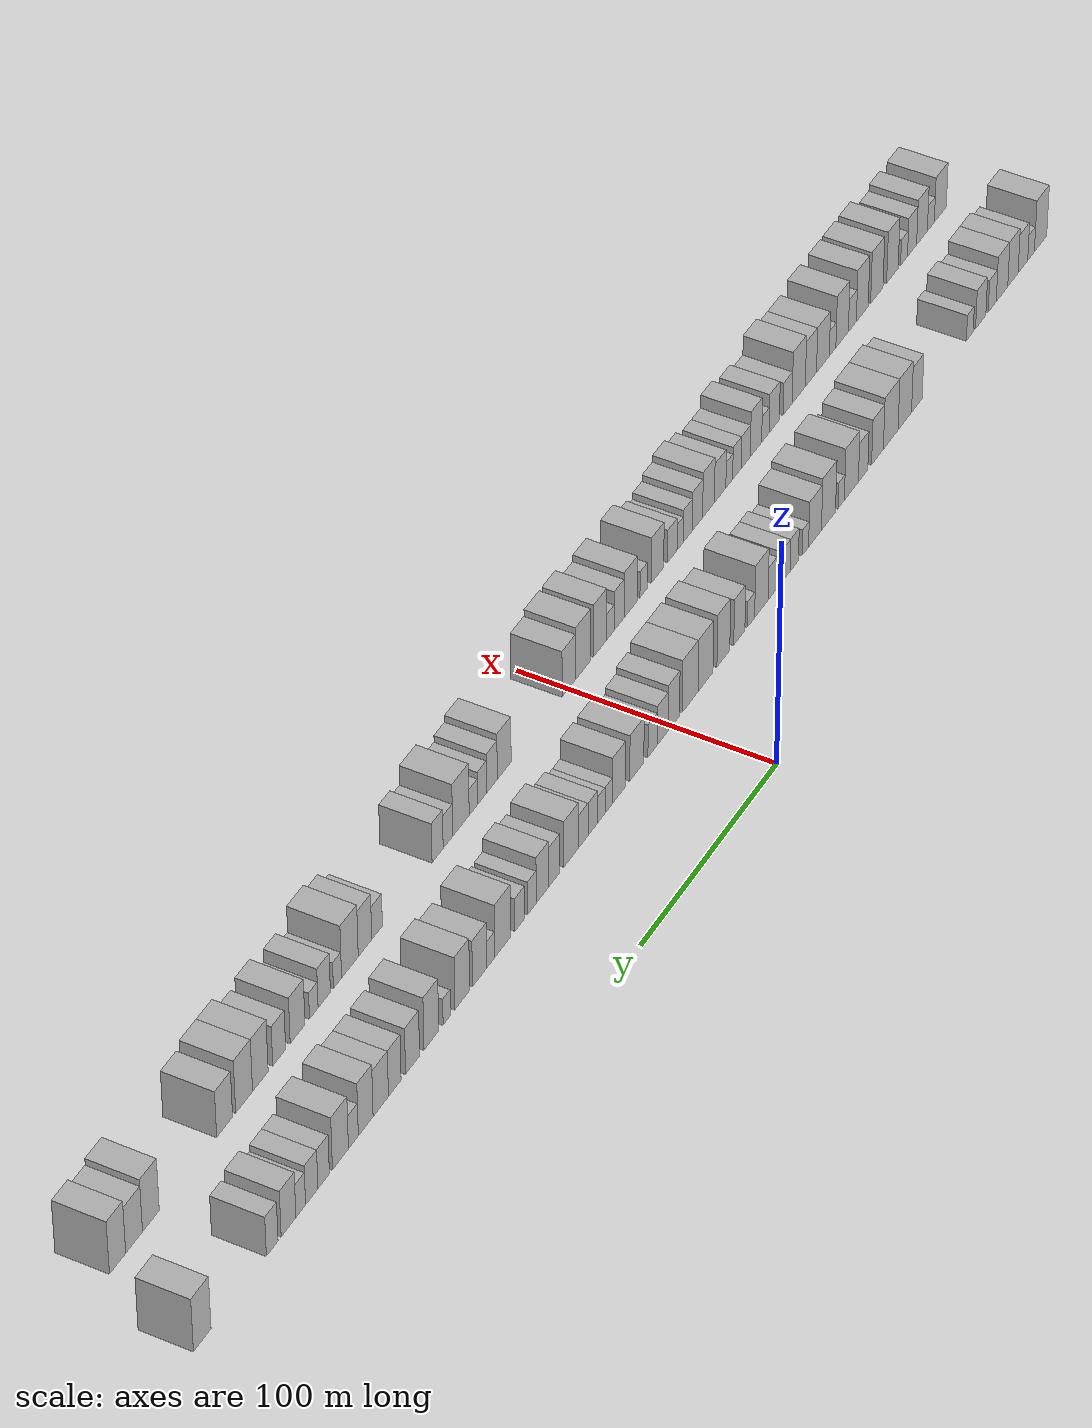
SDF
<sdf version="1.6">
 <world name="default">
  <scene>
   <sky><clouds><speed>12</speed></clouds></sky>
   <ambient>0.4 0.4 0.4 1</ambient>
   <background>0.7 0.7 0.7 1</background>
   <shadows>1</shadows>
  </scene>
  <gravity>0 0 -9.8066</gravity>
  <magnetic_field>6e-06 2.3e-05 -4.2e-05</magnetic_field>
  <physics default="0" name="default_physics" type="ode">
   <ode>
    <solver>
     <type>quick</type>
     <iters>10</iters>
     <sor>1.0</sor>
     <use_dynamic_moi_rescaling>0</use_dynamic_moi_rescaling>
    </solver>
    <constraints>
     <cfm>0</cfm>
     <erp>0.2</erp>
     <contact_max_correcting_vel>100</contact_max_correcting_vel>
     <contact_surface_layer>0.001</contact_surface_layer>
    </constraints>
   </ode>
   <max_step_size>0.004</max_step_size>
   <real_time_factor>1</real_time_factor>
   <real_time_update_rate>250</real_time_update_rate>
  </physics>
  <light name="sun" type="directional">
   <pose>0 0 10 0 0 0</pose>
   <diffuse>0.8 0.8 0.8 1</diffuse>
   <specular>0.2 0.2 0.2 1</specular>
   <attenuation>
    <range>1000</range>
    <constant>0.9</constant>
    <linear>0.01</linear>
    <quadratic>0.001</quadratic>
   </attenuation>
   <direction>-0.5 0.1 -0.9</direction>
  </light>
  <model name="building_1">
   <static>1</static>
   <pose>50.0000 -294.7138 0 0.000000 0.000000 0.000000</pose>
   <link name="link">
    <pose>0 0 12.00 0 0 0</pose>
    <collision name="collision"><geometry><box><size>20.0000 10.5724 24.0000</size></box></geometry></collision>
    <visual name="visual">
     <cast_shadows>0</cast_shadows>
     <geometry><box><size>20.0000 10.5724 24.0000</size></box></geometry>
     <material>
      <script>
       <uri>model://HANNAS_wall/materials/scripts</uri>
       <uri>model://HANNAS_wall/materials/textures</uri>
       <name>vrc/HANNAS_wall</name>
      </script>
     </material>
    </visual>
   </link>
  </model>
  <model name="building_2">
   <static>1</static>
   <pose>50.0000 -286.5474 0 0.000000 0.000000 0.000000</pose>
   <link name="link">
    <pose>0 0 6.00 0 0 0</pose>
    <collision name="collision"><geometry><box><size>20.0000 5.7604 12.0000</size></box></geometry></collision>
    <visual name="visual">
     <cast_shadows>0</cast_shadows>
     <geometry><box><size>20.0000 5.7604 12.0000</size></box></geometry>
     <material>
      <script>
       <uri>model://HANNAS_wall/materials/scripts</uri>
       <uri>model://HANNAS_wall/materials/textures</uri>
       <name>vrc/HANNAS_wall</name>
      </script>
     </material>
    </visual>
   </link>
  </model>
  <model name="building_3">
   <static>1</static>
   <pose>50.0000 -279.5543 0 0.000000 0.000000 0.000000</pose>
   <link name="link">
    <pose>0 0 9.00 0 0 0</pose>
    <collision name="collision"><geometry><box><size>20.0000 8.2259 18.0000</size></box></geometry></collision>
    <visual name="visual">
     <cast_shadows>0</cast_shadows>
     <geometry><box><size>20.0000 8.2259 18.0000</size></box></geometry>
     <material>
      <script>
       <uri>model://HANNAS_wall/materials/scripts</uri>
       <uri>model://HANNAS_wall/materials/textures</uri>
       <name>vrc/HANNAS_wall</name>
      </script>
     </material>
    </visual>
   </link>
  </model>
  <model name="building_4">
   <static>1</static>
   <pose>50.0000 -271.0660 0 0.000000 0.000000 0.000000</pose>
   <link name="link">
    <pose>0 0 10.50 0 0 0</pose>
    <collision name="collision"><geometry><box><size>20.0000 8.7508 21.0000</size></box></geometry></collision>
    <visual name="visual">
     <cast_shadows>0</cast_shadows>
     <geometry><box><size>20.0000 8.7508 21.0000</size></box></geometry>
     <material>
      <script>
       <uri>model://HANNAS_wall/materials/scripts</uri>
       <uri>model://HANNAS_wall/materials/textures</uri>
       <name>vrc/HANNAS_wall</name>
      </script>
     </material>
    </visual>
   </link>
  </model>
  <model name="building_5">
   <static>1</static>
   <pose>50.0000 -261.7841 0 0.000000 0.000000 0.000000</pose>
   <link name="link">
    <pose>0 0 10.50 0 0 0</pose>
    <collision name="collision"><geometry><box><size>20.0000 9.8129 21.0000</size></box></geometry></collision>
    <visual name="visual">
     <cast_shadows>0</cast_shadows>
     <geometry><box><size>20.0000 9.8129 21.0000</size></box></geometry>
     <material>
      <script>
       <uri>model://HANNAS_wall/materials/scripts</uri>
       <uri>model://HANNAS_wall/materials/textures</uri>
       <name>vrc/HANNAS_wall</name>
      </script>
     </material>
    </visual>
   </link>
  </model>
  <model name="building_6">
   <static>1</static>
   <pose>50.0000 -253.4980 0 0.000000 0.000000 0.000000</pose>
   <link name="link">
    <pose>0 0 7.50 0 0 0</pose>
    <collision name="collision"><geometry><box><size>20.0000 6.7593 15.0000</size></box></geometry></collision>
    <visual name="visual">
     <cast_shadows>0</cast_shadows>
     <geometry><box><size>20.0000 6.7593 15.0000</size></box></geometry>
     <material>
      <script>
       <uri>model://HANNAS_wall/materials/scripts</uri>
       <uri>model://HANNAS_wall/materials/textures</uri>
       <name>vrc/HANNAS_wall</name>
      </script>
     </material>
    </visual>
   </link>
  </model>
  <model name="building_7">
   <static>1</static>
   <pose>50.0000 -243.8126 0 0.000000 0.000000 0.000000</pose>
   <link name="link">
    <pose>0 0 9.00 0 0 0</pose>
    <collision name="collision"><geometry><box><size>20.0000 8.6116 18.0000</size></box></geometry></collision>
    <visual name="visual">
     <cast_shadows>0</cast_shadows>
     <geometry><box><size>20.0000 8.6116 18.0000</size></box></geometry>
     <material>
      <script>
       <uri>model://HANNAS_wall/materials/scripts</uri>
       <uri>model://HANNAS_wall/materials/textures</uri>
       <name>vrc/HANNAS_wall</name>
      </script>
     </material>
    </visual>
   </link>
  </model>
  <model name="building_8">
   <static>1</static>
   <pose>50.0000 -234.6748 0 0.000000 0.000000 0.000000</pose>
   <link name="link">
    <pose>0 0 6.00 0 0 0</pose>
    <collision name="collision"><geometry><box><size>20.0000 5.6639 12.0000</size></box></geometry></collision>
    <visual name="visual">
     <cast_shadows>0</cast_shadows>
     <geometry><box><size>20.0000 5.6639 12.0000</size></box></geometry>
     <material>
      <script>
       <uri>model://HANNAS_wall/materials/scripts</uri>
       <uri>model://HANNAS_wall/materials/textures</uri>
       <name>vrc/HANNAS_wall</name>
      </script>
     </material>
    </visual>
   </link>
  </model>
  <model name="building_9">
   <static>1</static>
   <pose>50.0000 -190.8144 0 0.000000 0.000000 0.000000</pose>
   <link name="link">
    <pose>0 0 10.50 0 0 0</pose>
    <collision name="collision"><geometry><box><size>20.0000 8.6856 21.0000</size></box></geometry></collision>
    <visual name="visual">
     <cast_shadows>0</cast_shadows>
     <geometry><box><size>20.0000 8.6856 21.0000</size></box></geometry>
     <material>
      <script>
       <uri>model://HANNAS_wall/materials/scripts</uri>
       <uri>model://HANNAS_wall/materials/textures</uri>
       <name>vrc/HANNAS_wall</name>
      </script>
     </material>
    </visual>
   </link>
  </model>
  <model name="building_10">
   <static>1</static>
   <pose>50.0000 -180.9890 0 0.000000 0.000000 0.000000</pose>
   <link name="link">
    <pose>0 0 12.00 0 0 0</pose>
    <collision name="collision"><geometry><box><size>20.0000 10.9650 24.0000</size></box></geometry></collision>
    <visual name="visual">
     <cast_shadows>0</cast_shadows>
     <geometry><box><size>20.0000 10.9650 24.0000</size></box></geometry>
     <material>
      <script>
       <uri>model://HANNAS_wall/materials/scripts</uri>
       <uri>model://HANNAS_wall/materials/textures</uri>
       <name>vrc/HANNAS_wall</name>
      </script>
     </material>
    </visual>
   </link>
  </model>
  <model name="building_11">
   <static>1</static>
   <pose>50.0000 -169.5514 0 0.000000 0.000000 0.000000</pose>
   <link name="link">
    <pose>0 0 12.00 0 0 0</pose>
    <collision name="collision"><geometry><box><size>20.0000 11.9102 24.0000</size></box></geometry></collision>
    <visual name="visual">
     <cast_shadows>0</cast_shadows>
     <geometry><box><size>20.0000 11.9102 24.0000</size></box></geometry>
     <material>
      <script>
       <uri>model://HANNAS_wall/materials/scripts</uri>
       <uri>model://HANNAS_wall/materials/textures</uri>
       <name>vrc/HANNAS_wall</name>
      </script>
     </material>
    </visual>
   </link>
  </model>
  <model name="building_12">
   <static>1</static>
   <pose>50.0000 -158.8469 0 0.000000 0.000000 0.000000</pose>
   <link name="link">
    <pose>0 0 10.50 0 0 0</pose>
    <collision name="collision"><geometry><box><size>20.0000 9.4989 21.0000</size></box></geometry></collision>
    <visual name="visual">
     <cast_shadows>0</cast_shadows>
     <geometry><box><size>20.0000 9.4989 21.0000</size></box></geometry>
     <material>
      <script>
       <uri>model://HANNAS_wall/materials/scripts</uri>
       <uri>model://HANNAS_wall/materials/textures</uri>
       <name>vrc/HANNAS_wall</name>
      </script>
     </material>
    </visual>
   </link>
  </model>
  <model name="building_13">
   <static>1</static>
   <pose>50.0000 -147.2973 0 0.000000 0.000000 0.000000</pose>
   <link name="link">
    <pose>0 0 9.00 0 0 0</pose>
    <collision name="collision"><geometry><box><size>20.0000 7.6004 18.0000</size></box></geometry></collision>
    <visual name="visual">
     <cast_shadows>0</cast_shadows>
     <geometry><box><size>20.0000 7.6004 18.0000</size></box></geometry>
     <material>
      <script>
       <uri>model://HANNAS_wall/materials/scripts</uri>
       <uri>model://HANNAS_wall/materials/textures</uri>
       <name>vrc/HANNAS_wall</name>
      </script>
     </material>
    </visual>
   </link>
  </model>
  <model name="building_14">
   <static>1</static>
   <pose>50.0000 -137.9208 0 0.000000 0.000000 0.000000</pose>
   <link name="link">
    <pose>0 0 12.00 0 0 0</pose>
    <collision name="collision"><geometry><box><size>20.0000 11.1527 24.0000</size></box></geometry></collision>
    <visual name="visual">
     <cast_shadows>0</cast_shadows>
     <geometry><box><size>20.0000 11.1527 24.0000</size></box></geometry>
     <material>
      <script>
       <uri>model://HANNAS_wall/materials/scripts</uri>
       <uri>model://HANNAS_wall/materials/textures</uri>
       <name>vrc/HANNAS_wall</name>
      </script>
     </material>
    </visual>
   </link>
  </model>
  <model name="building_15">
   <static>1</static>
   <pose>50.0000 -129.8487 0 0.000000 0.000000 0.000000</pose>
   <link name="link">
    <pose>0 0 6.00 0 0 0</pose>
    <collision name="collision"><geometry><box><size>20.0000 4.9914 12.0000</size></box></geometry></collision>
    <visual name="visual">
     <cast_shadows>0</cast_shadows>
     <geometry><box><size>20.0000 4.9914 12.0000</size></box></geometry>
     <material>
      <script>
       <uri>model://HANNAS_wall/materials/scripts</uri>
       <uri>model://HANNAS_wall/materials/textures</uri>
       <name>vrc/HANNAS_wall</name>
      </script>
     </material>
    </visual>
   </link>
  </model>
  <model name="building_16">
   <static>1</static>
   <pose>50.0000 -119.7771 0 0.000000 0.000000 0.000000</pose>
   <link name="link">
    <pose>0 0 12.00 0 0 0</pose>
    <collision name="collision"><geometry><box><size>20.0000 11.1517 24.0000</size></box></geometry></collision>
    <visual name="visual">
     <cast_shadows>0</cast_shadows>
     <geometry><box><size>20.0000 11.1517 24.0000</size></box></geometry>
     <material>
      <script>
       <uri>model://HANNAS_wall/materials/scripts</uri>
       <uri>model://HANNAS_wall/materials/textures</uri>
       <name>vrc/HANNAS_wall</name>
      </script>
     </material>
    </visual>
   </link>
  </model>
  <model name="building_17">
   <static>1</static>
   <pose>50.0000 -109.1579 0 0.000000 0.000000 0.000000</pose>
   <link name="link">
    <pose>0 0 10.50 0 0 0</pose>
    <collision name="collision"><geometry><box><size>20.0000 10.0868 21.0000</size></box></geometry></collision>
    <visual name="visual">
     <cast_shadows>0</cast_shadows>
     <geometry><box><size>20.0000 10.0868 21.0000</size></box></geometry>
     <material>
      <script>
       <uri>model://HANNAS_wall/materials/scripts</uri>
       <uri>model://HANNAS_wall/materials/textures</uri>
       <name>vrc/HANNAS_wall</name>
      </script>
     </material>
    </visual>
   </link>
  </model>
  <model name="building_18">
   <static>1</static>
   <pose>50.0000 -101.6478 0 0.000000 0.000000 0.000000</pose>
   <link name="link">
    <pose>0 0 6.00 0 0 0</pose>
    <collision name="collision"><geometry><box><size>20.0000 4.9333 12.0000</size></box></geometry></collision>
    <visual name="visual">
     <cast_shadows>0</cast_shadows>
     <geometry><box><size>20.0000 4.9333 12.0000</size></box></geometry>
     <material>
      <script>
       <uri>model://HANNAS_wall/materials/scripts</uri>
       <uri>model://HANNAS_wall/materials/textures</uri>
       <name>vrc/HANNAS_wall</name>
      </script>
     </material>
    </visual>
   </link>
  </model>
  <model name="building_19">
   <static>1</static>
   <pose>50.0000 -92.9845 0 0.000000 0.000000 0.000000</pose>
   <link name="link">
    <pose>0 0 7.50 0 0 0</pose>
    <collision name="collision"><geometry><box><size>20.0000 6.3934 15.0000</size></box></geometry></collision>
    <visual name="visual">
     <cast_shadows>0</cast_shadows>
     <geometry><box><size>20.0000 6.3934 15.0000</size></box></geometry>
     <material>
      <script>
       <uri>model://HANNAS_wall/materials/scripts</uri>
       <uri>model://HANNAS_wall/materials/textures</uri>
       <name>vrc/HANNAS_wall</name>
      </script>
     </material>
    </visual>
   </link>
  </model>
  <model name="building_20">
   <static>1</static>
   <pose>50.0000 -86.0525 0 0.000000 0.000000 0.000000</pose>
   <link name="link">
    <pose>0 0 7.50 0 0 0</pose>
    <collision name="collision"><geometry><box><size>20.0000 7.4705 15.0000</size></box></geometry></collision>
    <visual name="visual">
     <cast_shadows>0</cast_shadows>
     <geometry><box><size>20.0000 7.4705 15.0000</size></box></geometry>
     <material>
      <script>
       <uri>model://HANNAS_wall/materials/scripts</uri>
       <uri>model://HANNAS_wall/materials/textures</uri>
       <name>vrc/HANNAS_wall</name>
      </script>
     </material>
    </visual>
   </link>
  </model>
  <model name="building_21">
   <static>1</static>
   <pose>50.0000 -75.9563 0 0.000000 0.000000 0.000000</pose>
   <link name="link">
    <pose>0 0 7.50 0 0 0</pose>
    <collision name="collision"><geometry><box><size>20.0000 6.7220 15.0000</size></box></geometry></collision>
    <visual name="visual">
     <cast_shadows>0</cast_shadows>
     <geometry><box><size>20.0000 6.7220 15.0000</size></box></geometry>
     <material>
      <script>
       <uri>model://HANNAS_wall/materials/scripts</uri>
       <uri>model://HANNAS_wall/materials/textures</uri>
       <name>vrc/HANNAS_wall</name>
      </script>
     </material>
    </visual>
   </link>
  </model>
  <model name="building_22">
   <static>1</static>
   <pose>50.0000 -67.4464 0 0.000000 0.000000 0.000000</pose>
   <link name="link">
    <pose>0 0 12.00 0 0 0</pose>
    <collision name="collision"><geometry><box><size>20.0000 10.2976 24.0000</size></box></geometry></collision>
    <visual name="visual">
     <cast_shadows>0</cast_shadows>
     <geometry><box><size>20.0000 10.2976 24.0000</size></box></geometry>
     <material>
      <script>
       <uri>model://HANNAS_wall/materials/scripts</uri>
       <uri>model://HANNAS_wall/materials/textures</uri>
       <name>vrc/HANNAS_wall</name>
      </script>
     </material>
    </visual>
   </link>
  </model>
  <model name="building_23">
   <static>1</static>
   <pose>50.0000 -59.5560 0 0.000000 0.000000 0.000000</pose>
   <link name="link">
    <pose>0 0 6.00 0 0 0</pose>
    <collision name="collision"><geometry><box><size>20.0000 5.4833 12.0000</size></box></geometry></collision>
    <visual name="visual">
     <cast_shadows>0</cast_shadows>
     <geometry><box><size>20.0000 5.4833 12.0000</size></box></geometry>
     <material>
      <script>
       <uri>model://HANNAS_wall/materials/scripts</uri>
       <uri>model://HANNAS_wall/materials/textures</uri>
       <name>vrc/HANNAS_wall</name>
      </script>
     </material>
    </visual>
   </link>
  </model>
  <model name="building_24">
   <static>1</static>
   <pose>50.0000 -50.5672 0 0.000000 0.000000 0.000000</pose>
   <link name="link">
    <pose>0 0 10.50 0 0 0</pose>
    <collision name="collision"><geometry><box><size>20.0000 8.4941 21.0000</size></box></geometry></collision>
    <visual name="visual">
     <cast_shadows>0</cast_shadows>
     <geometry><box><size>20.0000 8.4941 21.0000</size></box></geometry>
     <material>
      <script>
       <uri>model://HANNAS_wall/materials/scripts</uri>
       <uri>model://HANNAS_wall/materials/textures</uri>
       <name>vrc/HANNAS_wall</name>
      </script>
     </material>
    </visual>
   </link>
  </model>
  <model name="building_25">
   <static>1</static>
   <pose>50.0000 -38.4495 0 0.000000 0.000000 0.000000</pose>
   <link name="link">
    <pose>0 0 12.00 0 0 0</pose>
    <collision name="collision"><geometry><box><size>20.0000 9.7414 24.0000</size></box></geometry></collision>
    <visual name="visual">
     <cast_shadows>0</cast_shadows>
     <geometry><box><size>20.0000 9.7414 24.0000</size></box></geometry>
     <material>
      <script>
       <uri>model://HANNAS_wall/materials/scripts</uri>
       <uri>model://HANNAS_wall/materials/textures</uri>
       <name>vrc/HANNAS_wall</name>
      </script>
     </material>
    </visual>
   </link>
  </model>
  <model name="building_26">
   <static>1</static>
   <pose>50.0000 -24.9672 0 0.000000 0.000000 0.000000</pose>
   <link name="link">
    <pose>0 0 12.00 0 0 0</pose>
    <collision name="collision"><geometry><box><size>20.0000 11.2231 24.0000</size></box></geometry></collision>
    <visual name="visual">
     <cast_shadows>0</cast_shadows>
     <geometry><box><size>20.0000 11.2231 24.0000</size></box></geometry>
     <material>
      <script>
       <uri>model://HANNAS_wall/materials/scripts</uri>
       <uri>model://HANNAS_wall/materials/textures</uri>
       <name>vrc/HANNAS_wall</name>
      </script>
     </material>
    </visual>
   </link>
  </model>
  <model name="building_27">
   <static>1</static>
   <pose>50.0000 -13.4424 0 0.000000 0.000000 0.000000</pose>
   <link name="link">
    <pose>0 0 12.00 0 0 0</pose>
    <collision name="collision"><geometry><box><size>20.0000 11.8265 24.0000</size></box></geometry></collision>
    <visual name="visual">
     <cast_shadows>0</cast_shadows>
     <geometry><box><size>20.0000 11.8265 24.0000</size></box></geometry>
     <material>
      <script>
       <uri>model://HANNAS_wall/materials/scripts</uri>
       <uri>model://HANNAS_wall/materials/textures</uri>
       <name>vrc/HANNAS_wall</name>
      </script>
     </material>
    </visual>
   </link>
  </model>
  <model name="building_28">
   <static>1</static>
   <pose>50.0000 -1.2540 0 0.000000 0.000000 0.000000</pose>
   <link name="link">
    <pose>0 0 10.50 0 0 0</pose>
    <collision name="collision"><geometry><box><size>20.0000 8.5501 21.0000</size></box></geometry></collision>
    <visual name="visual">
     <cast_shadows>0</cast_shadows>
     <geometry><box><size>20.0000 8.5501 21.0000</size></box></geometry>
     <material>
      <script>
       <uri>model://HANNAS_wall/materials/scripts</uri>
       <uri>model://HANNAS_wall/materials/textures</uri>
       <name>vrc/HANNAS_wall</name>
      </script>
     </material>
    </visual>
   </link>
  </model>
  <model name="building_29">
   <static>1</static>
   <pose>50.0000 7.0445 0 0.000000 0.000000 0.000000</pose>
   <link name="link">
    <pose>0 0 9.00 0 0 0</pose>
    <collision name="collision"><geometry><box><size>20.0000 8.0470 18.0000</size></box></geometry></collision>
    <visual name="visual">
     <cast_shadows>0</cast_shadows>
     <geometry><box><size>20.0000 8.0470 18.0000</size></box></geometry>
     <material>
      <script>
       <uri>model://HANNAS_wall/materials/scripts</uri>
       <uri>model://HANNAS_wall/materials/textures</uri>
       <name>vrc/HANNAS_wall</name>
      </script>
     </material>
    </visual>
   </link>
  </model>
  <model name="building_30">
   <static>1</static>
   <pose>50.0000 14.4716 0 0.000000 0.000000 0.000000</pose>
   <link name="link">
    <pose>0 0 7.50 0 0 0</pose>
    <collision name="collision"><geometry><box><size>20.0000 6.8073 15.0000</size></box></geometry></collision>
    <visual name="visual">
     <cast_shadows>0</cast_shadows>
     <geometry><box><size>20.0000 6.8073 15.0000</size></box></geometry>
     <material>
      <script>
       <uri>model://HANNAS_wall/materials/scripts</uri>
       <uri>model://HANNAS_wall/materials/textures</uri>
       <name>vrc/HANNAS_wall</name>
      </script>
     </material>
    </visual>
   </link>
  </model>
  <model name="building_31">
   <static>1</static>
   <pose>50.0000 26.0191 0 0.000000 0.000000 0.000000</pose>
   <link name="link">
    <pose>0 0 10.50 0 0 0</pose>
    <collision name="collision"><geometry><box><size>20.0000 10.2875 21.0000</size></box></geometry></collision>
    <visual name="visual">
     <cast_shadows>0</cast_shadows>
     <geometry><box><size>20.0000 10.2875 21.0000</size></box></geometry>
     <material>
      <script>
       <uri>model://HANNAS_wall/materials/scripts</uri>
       <uri>model://HANNAS_wall/materials/textures</uri>
       <name>vrc/HANNAS_wall</name>
      </script>
     </material>
    </visual>
   </link>
  </model>
  <model name="building_32">
   <static>1</static>
   <pose>50.0000 38.9282 0 0.000000 0.000000 0.000000</pose>
   <link name="link">
    <pose>0 0 10.50 0 0 0</pose>
    <collision name="collision"><geometry><box><size>20.0000 9.5307 21.0000</size></box></geometry></collision>
    <visual name="visual">
     <cast_shadows>0</cast_shadows>
     <geometry><box><size>20.0000 9.5307 21.0000</size></box></geometry>
     <material>
      <script>
       <uri>model://HANNAS_wall/materials/scripts</uri>
       <uri>model://HANNAS_wall/materials/textures</uri>
       <name>vrc/HANNAS_wall</name>
      </script>
     </material>
    </visual>
   </link>
  </model>
  <model name="building_33">
   <static>1</static>
   <pose>50.0000 46.4095 0 0.000000 0.000000 0.000000</pose>
   <link name="link">
    <pose>0 0 6.00 0 0 0</pose>
    <collision name="collision"><geometry><box><size>20.0000 5.4320 12.0000</size></box></geometry></collision>
    <visual name="visual">
     <cast_shadows>0</cast_shadows>
     <geometry><box><size>20.0000 5.4320 12.0000</size></box></geometry>
     <material>
      <script>
       <uri>model://HANNAS_wall/materials/scripts</uri>
       <uri>model://HANNAS_wall/materials/textures</uri>
       <name>vrc/HANNAS_wall</name>
      </script>
     </material>
    </visual>
   </link>
  </model>
  <model name="building_34">
   <static>1</static>
   <pose>50.0000 51.8343 0 0.000000 0.000000 0.000000</pose>
   <link name="link">
    <pose>0 0 6.00 0 0 0</pose>
    <collision name="collision"><geometry><box><size>20.0000 5.4175 12.0000</size></box></geometry></collision>
    <visual name="visual">
     <cast_shadows>0</cast_shadows>
     <geometry><box><size>20.0000 5.4175 12.0000</size></box></geometry>
     <material>
      <script>
       <uri>model://HANNAS_wall/materials/scripts</uri>
       <uri>model://HANNAS_wall/materials/textures</uri>
       <name>vrc/HANNAS_wall</name>
      </script>
     </material>
    </visual>
   </link>
  </model>
  <model name="building_35">
   <static>1</static>
   <pose>50.0000 57.9451 0 0.000000 0.000000 0.000000</pose>
   <link name="link">
    <pose>0 0 7.50 0 0 0</pose>
    <collision name="collision"><geometry><box><size>20.0000 6.8042 15.0000</size></box></geometry></collision>
    <visual name="visual">
     <cast_shadows>0</cast_shadows>
     <geometry><box><size>20.0000 6.8042 15.0000</size></box></geometry>
     <material>
      <script>
       <uri>model://HANNAS_wall/materials/scripts</uri>
       <uri>model://HANNAS_wall/materials/textures</uri>
       <name>vrc/HANNAS_wall</name>
      </script>
     </material>
    </visual>
   </link>
  </model>
  <model name="building_36">
   <static>1</static>
   <pose>50.0000 64.7987 0 0.000000 0.000000 0.000000</pose>
   <link name="link">
    <pose>0 0 7.50 0 0 0</pose>
    <collision name="collision"><geometry><box><size>20.0000 6.9030 15.0000</size></box></geometry></collision>
    <visual name="visual">
     <cast_shadows>0</cast_shadows>
     <geometry><box><size>20.0000 6.9030 15.0000</size></box></geometry>
     <material>
      <script>
       <uri>model://HANNAS_wall/materials/scripts</uri>
       <uri>model://HANNAS_wall/materials/textures</uri>
       <name>vrc/HANNAS_wall</name>
      </script>
     </material>
    </visual>
   </link>
  </model>
  <model name="building_37">
   <static>1</static>
   <pose>50.0000 73.4553 0 0.000000 0.000000 0.000000</pose>
   <link name="link">
    <pose>0 0 10.50 0 0 0</pose>
    <collision name="collision"><geometry><box><size>20.0000 10.4101 21.0000</size></box></geometry></collision>
    <visual name="visual">
     <cast_shadows>0</cast_shadows>
     <geometry><box><size>20.0000 10.4101 21.0000</size></box></geometry>
     <material>
      <script>
       <uri>model://HANNAS_wall/materials/scripts</uri>
       <uri>model://HANNAS_wall/materials/textures</uri>
       <name>vrc/HANNAS_wall</name>
      </script>
     </material>
    </visual>
   </link>
  </model>
  <model name="building_38">
   <static>1</static>
   <pose>50.0000 85.5674 0 0.000000 0.000000 0.000000</pose>
   <link name="link">
    <pose>0 0 9.00 0 0 0</pose>
    <collision name="collision"><geometry><box><size>20.0000 7.8140 18.0000</size></box></geometry></collision>
    <visual name="visual">
     <cast_shadows>0</cast_shadows>
     <geometry><box><size>20.0000 7.8140 18.0000</size></box></geometry>
     <material>
      <script>
       <uri>model://HANNAS_wall/materials/scripts</uri>
       <uri>model://HANNAS_wall/materials/textures</uri>
       <name>vrc/HANNAS_wall</name>
      </script>
     </material>
    </visual>
   </link>
  </model>
  <model name="building_39">
   <static>1</static>
   <pose>50.0000 93.9009 0 0.000000 0.000000 0.000000</pose>
   <link name="link">
    <pose>0 0 10.50 0 0 0</pose>
    <collision name="collision"><geometry><box><size>20.0000 8.8532 21.0000</size></box></geometry></collision>
    <visual name="visual">
     <cast_shadows>0</cast_shadows>
     <geometry><box><size>20.0000 8.8532 21.0000</size></box></geometry>
     <material>
      <script>
       <uri>model://HANNAS_wall/materials/scripts</uri>
       <uri>model://HANNAS_wall/materials/textures</uri>
       <name>vrc/HANNAS_wall</name>
      </script>
     </material>
    </visual>
   </link>
  </model>
  <model name="building_40">
   <static>1</static>
   <pose>50.0000 101.3435 0 0.000000 0.000000 0.000000</pose>
   <link name="link">
    <pose>0 0 7.50 0 0 0</pose>
    <collision name="collision"><geometry><box><size>20.0000 6.0319 15.0000</size></box></geometry></collision>
    <visual name="visual">
     <cast_shadows>0</cast_shadows>
     <geometry><box><size>20.0000 6.0319 15.0000</size></box></geometry>
     <material>
      <script>
       <uri>model://HANNAS_wall/materials/scripts</uri>
       <uri>model://HANNAS_wall/materials/textures</uri>
       <name>vrc/HANNAS_wall</name>
      </script>
     </material>
    </visual>
   </link>
  </model>
  <model name="building_41">
   <static>1</static>
   <pose>50.0000 109.8195 0 0.000000 0.000000 0.000000</pose>
   <link name="link">
    <pose>0 0 7.50 0 0 0</pose>
    <collision name="collision"><geometry><box><size>20.0000 6.9199 15.0000</size></box></geometry></collision>
    <visual name="visual">
     <cast_shadows>0</cast_shadows>
     <geometry><box><size>20.0000 6.9199 15.0000</size></box></geometry>
     <material>
      <script>
       <uri>model://HANNAS_wall/materials/scripts</uri>
       <uri>model://HANNAS_wall/materials/textures</uri>
       <name>vrc/HANNAS_wall</name>
      </script>
     </material>
    </visual>
   </link>
  </model>
  <model name="building_42">
   <static>1</static>
   <pose>50.0000 121.7617 0 0.000000 0.000000 0.000000</pose>
   <link name="link">
    <pose>0 0 12.00 0 0 0</pose>
    <collision name="collision"><geometry><box><size>20.0000 10.9646 24.0000</size></box></geometry></collision>
    <visual name="visual">
     <cast_shadows>0</cast_shadows>
     <geometry><box><size>20.0000 10.9646 24.0000</size></box></geometry>
     <material>
      <script>
       <uri>model://HANNAS_wall/materials/scripts</uri>
       <uri>model://HANNAS_wall/materials/textures</uri>
       <name>vrc/HANNAS_wall</name>
      </script>
     </material>
    </visual>
   </link>
  </model>
  <model name="building_43">
   <static>1</static>
   <pose>50.0000 130.1045 0 0.000000 0.000000 0.000000</pose>
   <link name="link">
    <pose>0 0 6.00 0 0 0</pose>
    <collision name="collision"><geometry><box><size>20.0000 5.7210 12.0000</size></box></geometry></collision>
    <visual name="visual">
     <cast_shadows>0</cast_shadows>
     <geometry><box><size>20.0000 5.7210 12.0000</size></box></geometry>
     <material>
      <script>
       <uri>model://HANNAS_wall/materials/scripts</uri>
       <uri>model://HANNAS_wall/materials/textures</uri>
       <name>vrc/HANNAS_wall</name>
      </script>
     </material>
    </visual>
   </link>
  </model>
  <model name="building_44">
   <static>1</static>
   <pose>50.0000 137.8530 0 0.000000 0.000000 0.000000</pose>
   <link name="link">
    <pose>0 0 10.50 0 0 0</pose>
    <collision name="collision"><geometry><box><size>20.0000 9.7760 21.0000</size></box></geometry></collision>
    <visual name="visual">
     <cast_shadows>0</cast_shadows>
     <geometry><box><size>20.0000 9.7760 21.0000</size></box></geometry>
     <material>
      <script>
       <uri>model://HANNAS_wall/materials/scripts</uri>
       <uri>model://HANNAS_wall/materials/textures</uri>
       <name>vrc/HANNAS_wall</name>
      </script>
     </material>
    </visual>
   </link>
  </model>
  <model name="building_45">
   <static>1</static>
   <pose>50.0000 149.7841 0 0.000000 0.000000 0.000000</pose>
   <link name="link">
    <pose>0 0 12.00 0 0 0</pose>
    <collision name="collision"><geometry><box><size>20.0000 10.0864 24.0000</size></box></geometry></collision>
    <visual name="visual">
     <cast_shadows>0</cast_shadows>
     <geometry><box><size>20.0000 10.0864 24.0000</size></box></geometry>
     <material>
      <script>
       <uri>model://HANNAS_wall/materials/scripts</uri>
       <uri>model://HANNAS_wall/materials/textures</uri>
       <name>vrc/HANNAS_wall</name>
      </script>
     </material>
    </visual>
   </link>
  </model>
  <model name="building_46">
   <static>1</static>
   <pose>50.0000 160.3457 0 0.000000 0.000000 0.000000</pose>
   <link name="link">
    <pose>0 0 6.00 0 0 0</pose>
    <collision name="collision"><geometry><box><size>20.0000 5.0367 12.0000</size></box></geometry></collision>
    <visual name="visual">
     <cast_shadows>0</cast_shadows>
     <geometry><box><size>20.0000 5.0367 12.0000</size></box></geometry>
     <material>
      <script>
       <uri>model://HANNAS_wall/materials/scripts</uri>
       <uri>model://HANNAS_wall/materials/textures</uri>
       <name>vrc/HANNAS_wall</name>
      </script>
     </material>
    </visual>
   </link>
  </model>
  <model name="building_47">
   <static>1</static>
   <pose>50.0000 170.8493 0 0.000000 0.000000 0.000000</pose>
   <link name="link">
    <pose>0 0 12.00 0 0 0</pose>
    <collision name="collision"><geometry><box><size>20.0000 9.9705 24.0000</size></box></geometry></collision>
    <visual name="visual">
     <cast_shadows>0</cast_shadows>
     <geometry><box><size>20.0000 9.9705 24.0000</size></box></geometry>
     <material>
      <script>
       <uri>model://HANNAS_wall/materials/scripts</uri>
       <uri>model://HANNAS_wall/materials/textures</uri>
       <name>vrc/HANNAS_wall</name>
      </script>
     </material>
    </visual>
   </link>
  </model>
  <model name="building_48">
   <static>1</static>
   <pose>50.0000 183.5545 0 0.000000 0.000000 0.000000</pose>
   <link name="link">
    <pose>0 0 10.50 0 0 0</pose>
    <collision name="collision"><geometry><box><size>20.0000 9.4399 21.0000</size></box></geometry></collision>
    <visual name="visual">
     <cast_shadows>0</cast_shadows>
     <geometry><box><size>20.0000 9.4399 21.0000</size></box></geometry>
     <material>
      <script>
       <uri>model://HANNAS_wall/materials/scripts</uri>
       <uri>model://HANNAS_wall/materials/textures</uri>
       <name>vrc/HANNAS_wall</name>
      </script>
     </material>
    </visual>
   </link>
  </model>
  <model name="building_49">
   <static>1</static>
   <pose>50.0000 195.4956 0 0.000000 0.000000 0.000000</pose>
   <link name="link">
    <pose>0 0 10.50 0 0 0</pose>
    <collision name="collision"><geometry><box><size>20.0000 8.4423 21.0000</size></box></geometry></collision>
    <visual name="visual">
     <cast_shadows>0</cast_shadows>
     <geometry><box><size>20.0000 8.4423 21.0000</size></box></geometry>
     <material>
      <script>
       <uri>model://HANNAS_wall/materials/scripts</uri>
       <uri>model://HANNAS_wall/materials/textures</uri>
       <name>vrc/HANNAS_wall</name>
      </script>
     </material>
    </visual>
   </link>
  </model>
  <model name="building_50">
   <static>1</static>
   <pose>50.0000 204.8326 0 0.000000 0.000000 0.000000</pose>
   <link name="link">
    <pose>0 0 10.50 0 0 0</pose>
    <collision name="collision"><geometry><box><size>20.0000 10.2317 21.0000</size></box></geometry></collision>
    <visual name="visual">
     <cast_shadows>0</cast_shadows>
     <geometry><box><size>20.0000 10.2317 21.0000</size></box></geometry>
     <material>
      <script>
       <uri>model://HANNAS_wall/materials/scripts</uri>
       <uri>model://HANNAS_wall/materials/textures</uri>
       <name>vrc/HANNAS_wall</name>
      </script>
     </material>
    </visual>
   </link>
  </model>
  <model name="building_51">
   <static>1</static>
   <pose>50.0000 214.8305 0 0.000000 0.000000 0.000000</pose>
   <link name="link">
    <pose>0 0 12.00 0 0 0</pose>
    <collision name="collision"><geometry><box><size>20.0000 9.7640 24.0000</size></box></geometry></collision>
    <visual name="visual">
     <cast_shadows>0</cast_shadows>
     <geometry><box><size>20.0000 9.7640 24.0000</size></box></geometry>
     <material>
      <script>
       <uri>model://HANNAS_wall/materials/scripts</uri>
       <uri>model://HANNAS_wall/materials/textures</uri>
       <name>vrc/HANNAS_wall</name>
      </script>
     </material>
    </visual>
   </link>
  </model>
  <model name="building_52">
   <static>1</static>
   <pose>50.0000 222.9676 0 0.000000 0.000000 0.000000</pose>
   <link name="link">
    <pose>0 0 7.50 0 0 0</pose>
    <collision name="collision"><geometry><box><size>20.0000 6.5101 15.0000</size></box></geometry></collision>
    <visual name="visual">
     <cast_shadows>0</cast_shadows>
     <geometry><box><size>20.0000 6.5101 15.0000</size></box></geometry>
     <material>
      <script>
       <uri>model://HANNAS_wall/materials/scripts</uri>
       <uri>model://HANNAS_wall/materials/textures</uri>
       <name>vrc/HANNAS_wall</name>
      </script>
     </material>
    </visual>
   </link>
  </model>
  <model name="building_53">
   <static>1</static>
   <pose>50.0000 231.4783 0 0.000000 0.000000 0.000000</pose>
   <link name="link">
    <pose>0 0 12.00 0 0 0</pose>
    <collision name="collision"><geometry><box><size>20.0000 10.5115 24.0000</size></box></geometry></collision>
    <visual name="visual">
     <cast_shadows>0</cast_shadows>
     <geometry><box><size>20.0000 10.5115 24.0000</size></box></geometry>
     <material>
      <script>
       <uri>model://HANNAS_wall/materials/scripts</uri>
       <uri>model://HANNAS_wall/materials/textures</uri>
       <name>vrc/HANNAS_wall</name>
      </script>
     </material>
    </visual>
   </link>
  </model>
  <model name="building_54">
   <static>1</static>
   <pose>50.0000 242.4582 0 0.000000 0.000000 0.000000</pose>
   <link name="link">
    <pose>0 0 9.00 0 0 0</pose>
    <collision name="collision"><geometry><box><size>20.0000 7.4483 18.0000</size></box></geometry></collision>
    <visual name="visual">
     <cast_shadows>0</cast_shadows>
     <geometry><box><size>20.0000 7.4483 18.0000</size></box></geometry>
     <material>
      <script>
       <uri>model://HANNAS_wall/materials/scripts</uri>
       <uri>model://HANNAS_wall/materials/textures</uri>
       <name>vrc/HANNAS_wall</name>
      </script>
     </material>
    </visual>
   </link>
  </model>
  <model name="building_55">
   <static>1</static>
   <pose>50.0000 250.1970 0 0.000000 0.000000 0.000000</pose>
   <link name="link">
    <pose>0 0 9.00 0 0 0</pose>
    <collision name="collision"><geometry><box><size>20.0000 8.0293 18.0000</size></box></geometry></collision>
    <visual name="visual">
     <cast_shadows>0</cast_shadows>
     <geometry><box><size>20.0000 8.0293 18.0000</size></box></geometry>
     <material>
      <script>
       <uri>model://HANNAS_wall/materials/scripts</uri>
       <uri>model://HANNAS_wall/materials/textures</uri>
       <name>vrc/HANNAS_wall</name>
      </script>
     </material>
    </visual>
   </link>
  </model>
  <model name="building_56">
   <static>1</static>
   <pose>50.0000 257.3411 0 0.000000 0.000000 0.000000</pose>
   <link name="link">
    <pose>0 0 7.50 0 0 0</pose>
    <collision name="collision"><geometry><box><size>20.0000 6.2587 15.0000</size></box></geometry></collision>
    <visual name="visual">
     <cast_shadows>0</cast_shadows>
     <geometry><box><size>20.0000 6.2587 15.0000</size></box></geometry>
     <material>
      <script>
       <uri>model://HANNAS_wall/materials/scripts</uri>
       <uri>model://HANNAS_wall/materials/textures</uri>
       <name>vrc/HANNAS_wall</name>
      </script>
     </material>
    </visual>
   </link>
  </model>
  <model name="building_57">
   <static>1</static>
   <pose>50.0000 265.2137 0 0.000000 0.000000 0.000000</pose>
   <link name="link">
    <pose>0 0 10.50 0 0 0</pose>
    <collision name="collision"><geometry><box><size>20.0000 9.4865 21.0000</size></box></geometry></collision>
    <visual name="visual">
     <cast_shadows>0</cast_shadows>
     <geometry><box><size>20.0000 9.4865 21.0000</size></box></geometry>
     <material>
      <script>
       <uri>model://HANNAS_wall/materials/scripts</uri>
       <uri>model://HANNAS_wall/materials/textures</uri>
       <name>vrc/HANNAS_wall</name>
      </script>
     </material>
    </visual>
   </link>
  </model>
  <model name="building_58">
   <static>1</static>
   <pose>50.0000 275.6869 0 0.000000 0.000000 0.000000</pose>
   <link name="link">
    <pose>0 0 9.00 0 0 0</pose>
    <collision name="collision"><geometry><box><size>20.0000 7.4600 18.0000</size></box></geometry></collision>
    <visual name="visual">
     <cast_shadows>0</cast_shadows>
     <geometry><box><size>20.0000 7.4600 18.0000</size></box></geometry>
     <material>
      <script>
       <uri>model://HANNAS_wall/materials/scripts</uri>
       <uri>model://HANNAS_wall/materials/textures</uri>
       <name>vrc/HANNAS_wall</name>
      </script>
     </material>
    </visual>
   </link>
  </model>
  <model name="building_59">
   <static>1</static>
   <pose>50.0000 319.8931 0 0.000000 0.000000 0.000000</pose>
   <link name="link">
    <pose>0 0 12.00 0 0 0</pose>
    <collision name="collision"><geometry><box><size>20.0000 10.9841 24.0000</size></box></geometry></collision>
    <visual name="visual">
     <cast_shadows>0</cast_shadows>
     <geometry><box><size>20.0000 10.9841 24.0000</size></box></geometry>
     <material>
      <script>
       <uri>model://HANNAS_wall/materials/scripts</uri>
       <uri>model://HANNAS_wall/materials/textures</uri>
       <name>vrc/HANNAS_wall</name>
      </script>
     </material>
    </visual>
   </link>
  </model>
  <model name="building_60">
   <static>1</static>
   <pose>90.0000 -292.9377 0 0.000000 0.000000 0.000000</pose>
   <link name="link">
    <pose>0 0 10.50 0 0 0</pose>
    <collision name="collision"><geometry><box><size>20.0000 10.1247 21.0000</size></box></geometry></collision>
    <visual name="visual">
     <cast_shadows>0</cast_shadows>
     <geometry><box><size>20.0000 10.1247 21.0000</size></box></geometry>
     <material>
      <script>
       <uri>model://HANNAS_wall/materials/scripts</uri>
       <uri>model://HANNAS_wall/materials/textures</uri>
       <name>vrc/HANNAS_wall</name>
      </script>
     </material>
    </visual>
   </link>
  </model>
  <model name="building_61">
   <static>1</static>
   <pose>90.0000 -284.9305 0 0.000000 0.000000 0.000000</pose>
   <link name="link">
    <pose>0 0 6.00 0 0 0</pose>
    <collision name="collision"><geometry><box><size>20.0000 5.8897 12.0000</size></box></geometry></collision>
    <visual name="visual">
     <cast_shadows>0</cast_shadows>
     <geometry><box><size>20.0000 5.8897 12.0000</size></box></geometry>
     <material>
      <script>
       <uri>model://HANNAS_wall/materials/scripts</uri>
       <uri>model://HANNAS_wall/materials/textures</uri>
       <name>vrc/HANNAS_wall</name>
      </script>
     </material>
    </visual>
   </link>
  </model>
  <model name="building_62">
   <static>1</static>
   <pose>90.0000 -277.4598 0 0.000000 0.000000 0.000000</pose>
   <link name="link">
    <pose>0 0 10.50 0 0 0</pose>
    <collision name="collision"><geometry><box><size>20.0000 9.0517 21.0000</size></box></geometry></collision>
    <visual name="visual">
     <cast_shadows>0</cast_shadows>
     <geometry><box><size>20.0000 9.0517 21.0000</size></box></geometry>
     <material>
      <script>
       <uri>model://HANNAS_wall/materials/scripts</uri>
       <uri>model://HANNAS_wall/materials/textures</uri>
       <name>vrc/HANNAS_wall</name>
      </script>
     </material>
    </visual>
   </link>
  </model>
  <model name="building_63">
   <static>1</static>
   <pose>90.0000 -269.1198 0 0.000000 0.000000 0.000000</pose>
   <link name="link">
    <pose>0 0 9.00 0 0 0</pose>
    <collision name="collision"><geometry><box><size>20.0000 7.6284 18.0000</size></box></geometry></collision>
    <visual name="visual">
     <cast_shadows>0</cast_shadows>
     <geometry><box><size>20.0000 7.6284 18.0000</size></box></geometry>
     <material>
      <script>
       <uri>model://HANNAS_wall/materials/scripts</uri>
       <uri>model://HANNAS_wall/materials/textures</uri>
       <name>vrc/HANNAS_wall</name>
      </script>
     </material>
    </visual>
   </link>
  </model>
  <model name="building_64">
   <static>1</static>
   <pose>90.0000 -262.4102 0 0.000000 0.000000 0.000000</pose>
   <link name="link">
    <pose>0 0 6.00 0 0 0</pose>
    <collision name="collision"><geometry><box><size>20.0000 5.7907 12.0000</size></box></geometry></collision>
    <visual name="visual">
     <cast_shadows>0</cast_shadows>
     <geometry><box><size>20.0000 5.7907 12.0000</size></box></geometry>
     <material>
      <script>
       <uri>model://HANNAS_wall/materials/scripts</uri>
       <uri>model://HANNAS_wall/materials/textures</uri>
       <name>vrc/HANNAS_wall</name>
      </script>
     </material>
    </visual>
   </link>
  </model>
  <model name="building_65">
   <static>1</static>
   <pose>90.0000 -252.6996 0 0.000000 0.000000 0.000000</pose>
   <link name="link">
    <pose>0 0 12.00 0 0 0</pose>
    <collision name="collision"><geometry><box><size>20.0000 9.6305 24.0000</size></box></geometry></collision>
    <visual name="visual">
     <cast_shadows>0</cast_shadows>
     <geometry><box><size>20.0000 9.6305 24.0000</size></box></geometry>
     <material>
      <script>
       <uri>model://HANNAS_wall/materials/scripts</uri>
       <uri>model://HANNAS_wall/materials/textures</uri>
       <name>vrc/HANNAS_wall</name>
      </script>
     </material>
    </visual>
   </link>
  </model>
  <model name="building_66">
   <static>1</static>
   <pose>90.0000 -239.7801 0 0.000000 0.000000 0.000000</pose>
   <link name="link">
    <pose>0 0 12.00 0 0 0</pose>
    <collision name="collision"><geometry><box><size>20.0000 10.2086 24.0000</size></box></geometry></collision>
    <visual name="visual">
     <cast_shadows>0</cast_shadows>
     <geometry><box><size>20.0000 10.2086 24.0000</size></box></geometry>
     <material>
      <script>
       <uri>model://HANNAS_wall/materials/scripts</uri>
       <uri>model://HANNAS_wall/materials/textures</uri>
       <name>vrc/HANNAS_wall</name>
      </script>
     </material>
    </visual>
   </link>
  </model>
  <model name="building_67">
   <static>1</static>
   <pose>90.0000 -227.8068 0 0.000000 0.000000 0.000000</pose>
   <link name="link">
    <pose>0 0 12.00 0 0 0</pose>
    <collision name="collision"><geometry><box><size>20.0000 9.7381 24.0000</size></box></geometry></collision>
    <visual name="visual">
     <cast_shadows>0</cast_shadows>
     <geometry><box><size>20.0000 9.7381 24.0000</size></box></geometry>
     <material>
      <script>
       <uri>model://HANNAS_wall/materials/scripts</uri>
       <uri>model://HANNAS_wall/materials/textures</uri>
       <name>vrc/HANNAS_wall</name>
      </script>
     </material>
    </visual>
   </link>
  </model>
  <model name="building_68">
   <static>1</static>
   <pose>90.0000 -219.6877 0 0.000000 0.000000 0.000000</pose>
   <link name="link">
    <pose>0 0 7.50 0 0 0</pose>
    <collision name="collision"><geometry><box><size>20.0000 6.5001 15.0000</size></box></geometry></collision>
    <visual name="visual">
     <cast_shadows>0</cast_shadows>
     <geometry><box><size>20.0000 6.5001 15.0000</size></box></geometry>
     <material>
      <script>
       <uri>model://HANNAS_wall/materials/scripts</uri>
       <uri>model://HANNAS_wall/materials/textures</uri>
       <name>vrc/HANNAS_wall</name>
      </script>
     </material>
    </visual>
   </link>
  </model>
  <model name="building_69">
   <static>1</static>
   <pose>90.0000 -211.3303 0 0.000000 0.000000 0.000000</pose>
   <link name="link">
    <pose>0 0 12.00 0 0 0</pose>
    <collision name="collision"><geometry><box><size>20.0000 10.2147 24.0000</size></box></geometry></collision>
    <visual name="visual">
     <cast_shadows>0</cast_shadows>
     <geometry><box><size>20.0000 10.2147 24.0000</size></box></geometry>
     <material>
      <script>
       <uri>model://HANNAS_wall/materials/scripts</uri>
       <uri>model://HANNAS_wall/materials/textures</uri>
       <name>vrc/HANNAS_wall</name>
      </script>
     </material>
    </visual>
   </link>
  </model>
  <model name="building_70">
   <static>1</static>
   <pose>90.0000 -203.5557 0 0.000000 0.000000 0.000000</pose>
   <link name="link">
    <pose>0 0 6.00 0 0 0</pose>
    <collision name="collision"><geometry><box><size>20.0000 5.3345 12.0000</size></box></geometry></collision>
    <visual name="visual">
     <cast_shadows>0</cast_shadows>
     <geometry><box><size>20.0000 5.3345 12.0000</size></box></geometry>
     <material>
      <script>
       <uri>model://HANNAS_wall/materials/scripts</uri>
       <uri>model://HANNAS_wall/materials/textures</uri>
       <name>vrc/HANNAS_wall</name>
      </script>
     </material>
    </visual>
   </link>
  </model>
  <model name="building_71">
   <static>1</static>
   <pose>90.0000 -195.7353 0 0.000000 0.000000 0.000000</pose>
   <link name="link">
    <pose>0 0 10.50 0 0 0</pose>
    <collision name="collision"><geometry><box><size>20.0000 10.3064 21.0000</size></box></geometry></collision>
    <visual name="visual">
     <cast_shadows>0</cast_shadows>
     <geometry><box><size>20.0000 10.3064 21.0000</size></box></geometry>
     <material>
      <script>
       <uri>model://HANNAS_wall/materials/scripts</uri>
       <uri>model://HANNAS_wall/materials/textures</uri>
       <name>vrc/HANNAS_wall</name>
      </script>
     </material>
    </visual>
   </link>
  </model>
  <model name="building_72">
   <static>1</static>
   <pose>90.0000 -186.0692 0 0.000000 0.000000 0.000000</pose>
   <link name="link">
    <pose>0 0 10.50 0 0 0</pose>
    <collision name="collision"><geometry><box><size>20.0000 9.0257 21.0000</size></box></geometry></collision>
    <visual name="visual">
     <cast_shadows>0</cast_shadows>
     <geometry><box><size>20.0000 9.0257 21.0000</size></box></geometry>
     <material>
      <script>
       <uri>model://HANNAS_wall/materials/scripts</uri>
       <uri>model://HANNAS_wall/materials/textures</uri>
       <name>vrc/HANNAS_wall</name>
      </script>
     </material>
    </visual>
   </link>
  </model>
  <model name="building_73">
   <static>1</static>
   <pose>90.0000 -176.2748 0 0.000000 0.000000 0.000000</pose>
   <link name="link">
    <pose>0 0 12.00 0 0 0</pose>
    <collision name="collision"><geometry><box><size>20.0000 10.5632 24.0000</size></box></geometry></collision>
    <visual name="visual">
     <cast_shadows>0</cast_shadows>
     <geometry><box><size>20.0000 10.5632 24.0000</size></box></geometry>
     <material>
      <script>
       <uri>model://HANNAS_wall/materials/scripts</uri>
       <uri>model://HANNAS_wall/materials/textures</uri>
       <name>vrc/HANNAS_wall</name>
      </script>
     </material>
    </visual>
   </link>
  </model>
  <model name="building_74">
   <static>1</static>
   <pose>90.0000 -167.4315 0 0.000000 0.000000 0.000000</pose>
   <link name="link">
    <pose>0 0 7.50 0 0 0</pose>
    <collision name="collision"><geometry><box><size>20.0000 7.1235 15.0000</size></box></geometry></collision>
    <visual name="visual">
     <cast_shadows>0</cast_shadows>
     <geometry><box><size>20.0000 7.1235 15.0000</size></box></geometry>
     <material>
      <script>
       <uri>model://HANNAS_wall/materials/scripts</uri>
       <uri>model://HANNAS_wall/materials/textures</uri>
       <name>vrc/HANNAS_wall</name>
      </script>
     </material>
    </visual>
   </link>
  </model>
  <model name="building_75">
   <static>1</static>
   <pose>90.0000 -156.7621 0 0.000000 0.000000 0.000000</pose>
   <link name="link">
    <pose>0 0 9.00 0 0 0</pose>
    <collision name="collision"><geometry><box><size>20.0000 8.2152 18.0000</size></box></geometry></collision>
    <visual name="visual">
     <cast_shadows>0</cast_shadows>
     <geometry><box><size>20.0000 8.2152 18.0000</size></box></geometry>
     <material>
      <script>
       <uri>model://HANNAS_wall/materials/scripts</uri>
       <uri>model://HANNAS_wall/materials/textures</uri>
       <name>vrc/HANNAS_wall</name>
      </script>
     </material>
    </visual>
   </link>
  </model>
  <model name="building_76">
   <static>1</static>
   <pose>90.0000 -149.7341 0 0.000000 0.000000 0.000000</pose>
   <link name="link">
    <pose>0 0 6.00 0 0 0</pose>
    <collision name="collision"><geometry><box><size>20.0000 5.8409 12.0000</size></box></geometry></collision>
    <visual name="visual">
     <cast_shadows>0</cast_shadows>
     <geometry><box><size>20.0000 5.8409 12.0000</size></box></geometry>
     <material>
      <script>
       <uri>model://HANNAS_wall/materials/scripts</uri>
       <uri>model://HANNAS_wall/materials/textures</uri>
       <name>vrc/HANNAS_wall</name>
      </script>
     </material>
    </visual>
   </link>
  </model>
  <model name="building_77">
   <static>1</static>
   <pose>90.0000 -142.3577 0 0.000000 0.000000 0.000000</pose>
   <link name="link">
    <pose>0 0 10.50 0 0 0</pose>
    <collision name="collision"><geometry><box><size>20.0000 8.9120 21.0000</size></box></geometry></collision>
    <visual name="visual">
     <cast_shadows>0</cast_shadows>
     <geometry><box><size>20.0000 8.9120 21.0000</size></box></geometry>
     <material>
      <script>
       <uri>model://HANNAS_wall/materials/scripts</uri>
       <uri>model://HANNAS_wall/materials/textures</uri>
       <name>vrc/HANNAS_wall</name>
      </script>
     </material>
    </visual>
   </link>
  </model>
  <model name="building_78">
   <static>1</static>
   <pose>90.0000 -134.3421 0 0.000000 0.000000 0.000000</pose>
   <link name="link">
    <pose>0 0 7.50 0 0 0</pose>
    <collision name="collision"><geometry><box><size>20.0000 7.1192 15.0000</size></box></geometry></collision>
    <visual name="visual">
     <cast_shadows>0</cast_shadows>
     <geometry><box><size>20.0000 7.1192 15.0000</size></box></geometry>
     <material>
      <script>
       <uri>model://HANNAS_wall/materials/scripts</uri>
       <uri>model://HANNAS_wall/materials/textures</uri>
       <name>vrc/HANNAS_wall</name>
      </script>
     </material>
    </visual>
   </link>
  </model>
  <model name="building_79">
   <static>1</static>
   <pose>90.0000 -127.4318 0 0.000000 0.000000 0.000000</pose>
   <link name="link">
    <pose>0 0 7.50 0 0 0</pose>
    <collision name="collision"><geometry><box><size>20.0000 6.7013 15.0000</size></box></geometry></collision>
    <visual name="visual">
     <cast_shadows>0</cast_shadows>
     <geometry><box><size>20.0000 6.7013 15.0000</size></box></geometry>
     <material>
      <script>
       <uri>model://HANNAS_wall/materials/scripts</uri>
       <uri>model://HANNAS_wall/materials/textures</uri>
       <name>vrc/HANNAS_wall</name>
      </script>
     </material>
    </visual>
   </link>
  </model>
  <model name="building_80">
   <static>1</static>
   <pose>90.0000 -121.4209 0 0.000000 0.000000 0.000000</pose>
   <link name="link">
    <pose>0 0 6.00 0 0 0</pose>
    <collision name="collision"><geometry><box><size>20.0000 5.3206 12.0000</size></box></geometry></collision>
    <visual name="visual">
     <cast_shadows>0</cast_shadows>
     <geometry><box><size>20.0000 5.3206 12.0000</size></box></geometry>
     <material>
      <script>
       <uri>model://HANNAS_wall/materials/scripts</uri>
       <uri>model://HANNAS_wall/materials/textures</uri>
       <name>vrc/HANNAS_wall</name>
      </script>
     </material>
    </visual>
   </link>
  </model>
  <model name="building_81">
   <static>1</static>
   <pose>90.0000 -114.3416 0 0.000000 0.000000 0.000000</pose>
   <link name="link">
    <pose>0 0 9.00 0 0 0</pose>
    <collision name="collision"><geometry><box><size>20.0000 8.8379 18.0000</size></box></geometry></collision>
    <visual name="visual">
     <cast_shadows>0</cast_shadows>
     <geometry><box><size>20.0000 8.8379 18.0000</size></box></geometry>
     <material>
      <script>
       <uri>model://HANNAS_wall/materials/scripts</uri>
       <uri>model://HANNAS_wall/materials/textures</uri>
       <name>vrc/HANNAS_wall</name>
      </script>
     </material>
    </visual>
   </link>
  </model>
  <model name="building_82">
   <static>1</static>
   <pose>90.0000 -105.3562 0 0.000000 0.000000 0.000000</pose>
   <link name="link">
    <pose>0 0 10.50 0 0 0</pose>
    <collision name="collision"><geometry><box><size>20.0000 9.1329 21.0000</size></box></geometry></collision>
    <visual name="visual">
     <cast_shadows>0</cast_shadows>
     <geometry><box><size>20.0000 9.1329 21.0000</size></box></geometry>
     <material>
      <script>
       <uri>model://HANNAS_wall/materials/scripts</uri>
       <uri>model://HANNAS_wall/materials/textures</uri>
       <name>vrc/HANNAS_wall</name>
      </script>
     </material>
    </visual>
   </link>
  </model>
  <model name="building_83">
   <static>1</static>
   <pose>90.0000 -96.8494 0 0.000000 0.000000 0.000000</pose>
   <link name="link">
    <pose>0 0 9.00 0 0 0</pose>
    <collision name="collision"><geometry><box><size>20.0000 7.8808 18.0000</size></box></geometry></collision>
    <visual name="visual">
     <cast_shadows>0</cast_shadows>
     <geometry><box><size>20.0000 7.8808 18.0000</size></box></geometry>
     <material>
      <script>
       <uri>model://HANNAS_wall/materials/scripts</uri>
       <uri>model://HANNAS_wall/materials/textures</uri>
       <name>vrc/HANNAS_wall</name>
      </script>
     </material>
    </visual>
   </link>
  </model>
  <model name="building_84">
   <static>1</static>
   <pose>90.0000 -89.4160 0 0.000000 0.000000 0.000000</pose>
   <link name="link">
    <pose>0 0 7.50 0 0 0</pose>
    <collision name="collision"><geometry><box><size>20.0000 6.9861 15.0000</size></box></geometry></collision>
    <visual name="visual">
     <cast_shadows>0</cast_shadows>
     <geometry><box><size>20.0000 6.9861 15.0000</size></box></geometry>
     <material>
      <script>
       <uri>model://HANNAS_wall/materials/scripts</uri>
       <uri>model://HANNAS_wall/materials/textures</uri>
       <name>vrc/HANNAS_wall</name>
      </script>
     </material>
    </visual>
   </link>
  </model>
  <model name="building_85">
   <static>1</static>
   <pose>90.0000 -83.5168 0 0.000000 0.000000 0.000000</pose>
   <link name="link">
    <pose>0 0 6.00 0 0 0</pose>
    <collision name="collision"><geometry><box><size>20.0000 4.8123 12.0000</size></box></geometry></collision>
    <visual name="visual">
     <cast_shadows>0</cast_shadows>
     <geometry><box><size>20.0000 4.8123 12.0000</size></box></geometry>
     <material>
      <script>
       <uri>model://HANNAS_wall/materials/scripts</uri>
       <uri>model://HANNAS_wall/materials/textures</uri>
       <name>vrc/HANNAS_wall</name>
      </script>
     </material>
    </visual>
   </link>
  </model>
  <model name="building_86">
   <static>1</static>
   <pose>90.0000 -77.5645 0 0.000000 0.000000 0.000000</pose>
   <link name="link">
    <pose>0 0 7.50 0 0 0</pose>
    <collision name="collision"><geometry><box><size>20.0000 7.0922 15.0000</size></box></geometry></collision>
    <visual name="visual">
     <cast_shadows>0</cast_shadows>
     <geometry><box><size>20.0000 7.0922 15.0000</size></box></geometry>
     <material>
      <script>
       <uri>model://HANNAS_wall/materials/scripts</uri>
       <uri>model://HANNAS_wall/materials/textures</uri>
       <name>vrc/HANNAS_wall</name>
      </script>
     </material>
    </visual>
   </link>
  </model>
  <model name="building_87">
   <static>1</static>
   <pose>90.0000 -66.3594 0 0.000000 0.000000 0.000000</pose>
   <link name="link">
    <pose>0 0 10.50 0 0 0</pose>
    <collision name="collision"><geometry><box><size>20.0000 9.3179 21.0000</size></box></geometry></collision>
    <visual name="visual">
     <cast_shadows>0</cast_shadows>
     <geometry><box><size>20.0000 9.3179 21.0000</size></box></geometry>
     <material>
      <script>
       <uri>model://HANNAS_wall/materials/scripts</uri>
       <uri>model://HANNAS_wall/materials/textures</uri>
       <name>vrc/HANNAS_wall</name>
      </script>
     </material>
    </visual>
   </link>
  </model>
  <model name="building_88">
   <static>1</static>
   <pose>90.0000 -55.8713 0 0.000000 0.000000 0.000000</pose>
   <link name="link">
    <pose>0 0 6.00 0 0 0</pose>
    <collision name="collision"><geometry><box><size>20.0000 5.6584 12.0000</size></box></geometry></collision>
    <visual name="visual">
     <cast_shadows>0</cast_shadows>
     <geometry><box><size>20.0000 5.6584 12.0000</size></box></geometry>
     <material>
      <script>
       <uri>model://HANNAS_wall/materials/scripts</uri>
       <uri>model://HANNAS_wall/materials/textures</uri>
       <name>vrc/HANNAS_wall</name>
      </script>
     </material>
    </visual>
   </link>
  </model>
  <model name="building_89">
   <static>1</static>
   <pose>90.0000 -46.0615 0 0.000000 0.000000 0.000000</pose>
   <link name="link">
    <pose>0 0 10.50 0 0 0</pose>
    <collision name="collision"><geometry><box><size>20.0000 9.9612 21.0000</size></box></geometry></collision>
    <visual name="visual">
     <cast_shadows>0</cast_shadows>
     <geometry><box><size>20.0000 9.9612 21.0000</size></box></geometry>
     <material>
      <script>
       <uri>model://HANNAS_wall/materials/scripts</uri>
       <uri>model://HANNAS_wall/materials/textures</uri>
       <name>vrc/HANNAS_wall</name>
      </script>
     </material>
    </visual>
   </link>
  </model>
  <model name="building_90">
   <static>1</static>
   <pose>90.0000 -37.4783 0 0.000000 0.000000 0.000000</pose>
   <link name="link">
    <pose>0 0 9.00 0 0 0</pose>
    <collision name="collision"><geometry><box><size>20.0000 7.2052 18.0000</size></box></geometry></collision>
    <visual name="visual">
     <cast_shadows>0</cast_shadows>
     <geometry><box><size>20.0000 7.2052 18.0000</size></box></geometry>
     <material>
      <script>
       <uri>model://HANNAS_wall/materials/scripts</uri>
       <uri>model://HANNAS_wall/materials/textures</uri>
       <name>vrc/HANNAS_wall</name>
      </script>
     </material>
    </visual>
   </link>
  </model>
  <model name="building_91">
   <static>1</static>
   <pose>90.0000 -31.0679 0 0.000000 0.000000 0.000000</pose>
   <link name="link">
    <pose>0 0 6.00 0 0 0</pose>
    <collision name="collision"><geometry><box><size>20.0000 5.6156 12.0000</size></box></geometry></collision>
    <visual name="visual">
     <cast_shadows>0</cast_shadows>
     <geometry><box><size>20.0000 5.6156 12.0000</size></box></geometry>
     <material>
      <script>
       <uri>model://HANNAS_wall/materials/scripts</uri>
       <uri>model://HANNAS_wall/materials/textures</uri>
       <name>vrc/HANNAS_wall</name>
      </script>
     </material>
    </visual>
   </link>
  </model>
  <model name="building_92">
   <static>1</static>
   <pose>90.0000 -23.3345 0 0.000000 0.000000 0.000000</pose>
   <link name="link">
    <pose>0 0 12.00 0 0 0</pose>
    <collision name="collision"><geometry><box><size>20.0000 9.8511 24.0000</size></box></geometry></collision>
    <visual name="visual">
     <cast_shadows>0</cast_shadows>
     <geometry><box><size>20.0000 9.8511 24.0000</size></box></geometry>
     <material>
      <script>
       <uri>model://HANNAS_wall/materials/scripts</uri>
       <uri>model://HANNAS_wall/materials/textures</uri>
       <name>vrc/HANNAS_wall</name>
      </script>
     </material>
    </visual>
   </link>
  </model>
  <model name="building_93">
   <static>1</static>
   <pose>90.0000 -10.8529 0 0.000000 0.000000 0.000000</pose>
   <link name="link">
    <pose>0 0 12.00 0 0 0</pose>
    <collision name="collision"><geometry><box><size>20.0000 11.1121 24.0000</size></box></geometry></collision>
    <visual name="visual">
     <cast_shadows>0</cast_shadows>
     <geometry><box><size>20.0000 11.1121 24.0000</size></box></geometry>
     <material>
      <script>
       <uri>model://HANNAS_wall/materials/scripts</uri>
       <uri>model://HANNAS_wall/materials/textures</uri>
       <name>vrc/HANNAS_wall</name>
      </script>
     </material>
    </visual>
   </link>
  </model>
  <model name="building_94">
   <static>1</static>
   <pose>90.0000 -0.3164 0 0.000000 0.000000 0.000000</pose>
   <link name="link">
    <pose>0 0 10.50 0 0 0</pose>
    <collision name="collision"><geometry><box><size>20.0000 9.9607 21.0000</size></box></geometry></collision>
    <visual name="visual">
     <cast_shadows>0</cast_shadows>
     <geometry><box><size>20.0000 9.9607 21.0000</size></box></geometry>
     <material>
      <script>
       <uri>model://HANNAS_wall/materials/scripts</uri>
       <uri>model://HANNAS_wall/materials/textures</uri>
       <name>vrc/HANNAS_wall</name>
      </script>
     </material>
    </visual>
   </link>
  </model>
  <model name="building_95">
   <static>1</static>
   <pose>90.0000 46.4864 0 0.000000 0.000000 0.000000</pose>
   <link name="link">
    <pose>0 0 10.50 0 0 0</pose>
    <collision name="collision"><geometry><box><size>20.0000 9.8816 21.0000</size></box></geometry></collision>
    <visual name="visual">
     <cast_shadows>0</cast_shadows>
     <geometry><box><size>20.0000 9.8816 21.0000</size></box></geometry>
     <material>
      <script>
       <uri>model://HANNAS_wall/materials/scripts</uri>
       <uri>model://HANNAS_wall/materials/textures</uri>
       <name>vrc/HANNAS_wall</name>
      </script>
     </material>
    </visual>
   </link>
  </model>
  <model name="building_96">
   <static>1</static>
   <pose>90.0000 55.2190 0 0.000000 0.000000 0.000000</pose>
   <link name="link">
    <pose>0 0 9.00 0 0 0</pose>
    <collision name="collision"><geometry><box><size>20.0000 7.5835 18.0000</size></box></geometry></collision>
    <visual name="visual">
     <cast_shadows>0</cast_shadows>
     <geometry><box><size>20.0000 7.5835 18.0000</size></box></geometry>
     <material>
      <script>
       <uri>model://HANNAS_wall/materials/scripts</uri>
       <uri>model://HANNAS_wall/materials/textures</uri>
       <name>vrc/HANNAS_wall</name>
      </script>
     </material>
    </visual>
   </link>
  </model>
  <model name="building_97">
   <static>1</static>
   <pose>90.0000 62.1937 0 0.000000 0.000000 0.000000</pose>
   <link name="link">
    <pose>0 0 7.50 0 0 0</pose>
    <collision name="collision"><geometry><box><size>20.0000 6.3659 15.0000</size></box></geometry></collision>
    <visual name="visual">
     <cast_shadows>0</cast_shadows>
     <geometry><box><size>20.0000 6.3659 15.0000</size></box></geometry>
     <material>
      <script>
       <uri>model://HANNAS_wall/materials/scripts</uri>
       <uri>model://HANNAS_wall/materials/textures</uri>
       <name>vrc/HANNAS_wall</name>
      </script>
     </material>
    </visual>
   </link>
  </model>
  <model name="building_98">
   <static>1</static>
   <pose>90.0000 68.3756 0 0.000000 0.000000 0.000000</pose>
   <link name="link">
    <pose>0 0 6.00 0 0 0</pose>
    <collision name="collision"><geometry><box><size>20.0000 5.9979 12.0000</size></box></geometry></collision>
    <visual name="visual">
     <cast_shadows>0</cast_shadows>
     <geometry><box><size>20.0000 5.9979 12.0000</size></box></geometry>
     <material>
      <script>
       <uri>model://HANNAS_wall/materials/scripts</uri>
       <uri>model://HANNAS_wall/materials/textures</uri>
       <name>vrc/HANNAS_wall</name>
      </script>
     </material>
    </visual>
   </link>
  </model>
  <model name="building_99">
   <static>1</static>
   <pose>90.0000 77.1770 0 0.000000 0.000000 0.000000</pose>
   <link name="link">
    <pose>0 0 12.00 0 0 0</pose>
    <collision name="collision"><geometry><box><size>20.0000 11.6049 24.0000</size></box></geometry></collision>
    <visual name="visual">
     <cast_shadows>0</cast_shadows>
     <geometry><box><size>20.0000 11.6049 24.0000</size></box></geometry>
     <material>
      <script>
       <uri>model://HANNAS_wall/materials/scripts</uri>
       <uri>model://HANNAS_wall/materials/textures</uri>
       <name>vrc/HANNAS_wall</name>
      </script>
     </material>
    </visual>
   </link>
  </model>
  <model name="building_100">
   <static>1</static>
   <pose>90.0000 86.3092 0 0.000000 0.000000 0.000000</pose>
   <link name="link">
    <pose>0 0 7.50 0 0 0</pose>
    <collision name="collision"><geometry><box><size>20.0000 6.6594 15.0000</size></box></geometry></collision>
    <visual name="visual">
     <cast_shadows>0</cast_shadows>
     <geometry><box><size>20.0000 6.6594 15.0000</size></box></geometry>
     <material>
      <script>
       <uri>model://HANNAS_wall/materials/scripts</uri>
       <uri>model://HANNAS_wall/materials/textures</uri>
       <name>vrc/HANNAS_wall</name>
      </script>
     </material>
    </visual>
   </link>
  </model>
  <model name="building_101">
   <static>1</static>
   <pose>90.0000 93.5126 0 0.000000 0.000000 0.000000</pose>
   <link name="link">
    <pose>0 0 9.00 0 0 0</pose>
    <collision name="collision"><geometry><box><size>20.0000 7.7475 18.0000</size></box></geometry></collision>
    <visual name="visual">
     <cast_shadows>0</cast_shadows>
     <geometry><box><size>20.0000 7.7475 18.0000</size></box></geometry>
     <material>
      <script>
       <uri>model://HANNAS_wall/materials/scripts</uri>
       <uri>model://HANNAS_wall/materials/textures</uri>
       <name>vrc/HANNAS_wall</name>
      </script>
     </material>
    </visual>
   </link>
  </model>
  <model name="building_102">
   <static>1</static>
   <pose>90.0000 135.2506 0 0.000000 0.000000 0.000000</pose>
   <link name="link">
    <pose>0 0 7.50 0 0 0</pose>
    <collision name="collision"><geometry><box><size>20.0000 7.2428 15.0000</size></box></geometry></collision>
    <visual name="visual">
     <cast_shadows>0</cast_shadows>
     <geometry><box><size>20.0000 7.2428 15.0000</size></box></geometry>
     <material>
      <script>
       <uri>model://HANNAS_wall/materials/scripts</uri>
       <uri>model://HANNAS_wall/materials/textures</uri>
       <name>vrc/HANNAS_wall</name>
      </script>
     </material>
    </visual>
   </link>
  </model>
  <model name="building_103">
   <static>1</static>
   <pose>90.0000 143.4629 0 0.000000 0.000000 0.000000</pose>
   <link name="link">
    <pose>0 0 10.50 0 0 0</pose>
    <collision name="collision"><geometry><box><size>20.0000 9.1817 21.0000</size></box></geometry></collision>
    <visual name="visual">
     <cast_shadows>0</cast_shadows>
     <geometry><box><size>20.0000 9.1817 21.0000</size></box></geometry>
     <material>
      <script>
       <uri>model://HANNAS_wall/materials/scripts</uri>
       <uri>model://HANNAS_wall/materials/textures</uri>
       <name>vrc/HANNAS_wall</name>
      </script>
     </material>
    </visual>
   </link>
  </model>
  <model name="building_104">
   <static>1</static>
   <pose>90.0000 153.6784 0 0.000000 0.000000 0.000000</pose>
   <link name="link">
    <pose>0 0 12.00 0 0 0</pose>
    <collision name="collision"><geometry><box><size>20.0000 11.2494 24.0000</size></box></geometry></collision>
    <visual name="visual">
     <cast_shadows>0</cast_shadows>
     <geometry><box><size>20.0000 11.2494 24.0000</size></box></geometry>
     <material>
      <script>
       <uri>model://HANNAS_wall/materials/scripts</uri>
       <uri>model://HANNAS_wall/materials/textures</uri>
       <name>vrc/HANNAS_wall</name>
      </script>
     </material>
    </visual>
   </link>
  </model>
  <model name="building_105">
   <static>1</static>
   <pose>90.0000 162.0528 0 0.000000 0.000000 0.000000</pose>
   <link name="link">
    <pose>0 0 6.00 0 0 0</pose>
    <collision name="collision"><geometry><box><size>20.0000 5.4996 12.0000</size></box></geometry></collision>
    <visual name="visual">
     <cast_shadows>0</cast_shadows>
     <geometry><box><size>20.0000 5.4996 12.0000</size></box></geometry>
     <material>
      <script>
       <uri>model://HANNAS_wall/materials/scripts</uri>
       <uri>model://HANNAS_wall/materials/textures</uri>
       <name>vrc/HANNAS_wall</name>
      </script>
     </material>
    </visual>
   </link>
  </model>
  <model name="building_106">
   <static>1</static>
   <pose>90.0000 170.9124 0 0.000000 0.000000 0.000000</pose>
   <link name="link">
    <pose>0 0 9.00 0 0 0</pose>
    <collision name="collision"><geometry><box><size>20.0000 8.2195 18.0000</size></box></geometry></collision>
    <visual name="visual">
     <cast_shadows>0</cast_shadows>
     <geometry><box><size>20.0000 8.2195 18.0000</size></box></geometry>
     <material>
      <script>
       <uri>model://HANNAS_wall/materials/scripts</uri>
       <uri>model://HANNAS_wall/materials/textures</uri>
       <name>vrc/HANNAS_wall</name>
      </script>
     </material>
    </visual>
   </link>
  </model>
  <model name="building_107">
   <static>1</static>
   <pose>90.0000 177.8979 0 0.000000 0.000000 0.000000</pose>
   <link name="link">
    <pose>0 0 6.00 0 0 0</pose>
    <collision name="collision"><geometry><box><size>20.0000 5.7516 12.0000</size></box></geometry></collision>
    <visual name="visual">
     <cast_shadows>0</cast_shadows>
     <geometry><box><size>20.0000 5.7516 12.0000</size></box></geometry>
     <material>
      <script>
       <uri>model://HANNAS_wall/materials/scripts</uri>
       <uri>model://HANNAS_wall/materials/textures</uri>
       <name>vrc/HANNAS_wall</name>
      </script>
     </material>
    </visual>
   </link>
  </model>
  <model name="building_108">
   <static>1</static>
   <pose>90.0000 188.6570 0 0.000000 0.000000 0.000000</pose>
   <link name="link">
    <pose>0 0 10.50 0 0 0</pose>
    <collision name="collision"><geometry><box><size>20.0000 9.7667 21.0000</size></box></geometry></collision>
    <visual name="visual">
     <cast_shadows>0</cast_shadows>
     <geometry><box><size>20.0000 9.7667 21.0000</size></box></geometry>
     <material>
      <script>
       <uri>model://HANNAS_wall/materials/scripts</uri>
       <uri>model://HANNAS_wall/materials/textures</uri>
       <name>vrc/HANNAS_wall</name>
      </script>
     </material>
    </visual>
   </link>
  </model>
  <model name="building_109">
   <static>1</static>
   <pose>90.0000 200.7852 0 0.000000 0.000000 0.000000</pose>
   <link name="link">
    <pose>0 0 9.00 0 0 0</pose>
    <collision name="collision"><geometry><box><size>20.0000 8.4896 18.0000</size></box></geometry></collision>
    <visual name="visual">
     <cast_shadows>0</cast_shadows>
     <geometry><box><size>20.0000 8.4896 18.0000</size></box></geometry>
     <material>
      <script>
       <uri>model://HANNAS_wall/materials/scripts</uri>
       <uri>model://HANNAS_wall/materials/textures</uri>
       <name>vrc/HANNAS_wall</name>
      </script>
     </material>
    </visual>
   </link>
  </model>
  <model name="building_110">
   <static>1</static>
   <pose>90.0000 213.1345 0 0.000000 0.000000 0.000000</pose>
   <link name="link">
    <pose>0 0 12.00 0 0 0</pose>
    <collision name="collision"><geometry><box><size>20.0000 10.2092 24.0000</size></box></geometry></collision>
    <visual name="visual">
     <cast_shadows>0</cast_shadows>
     <geometry><box><size>20.0000 10.2092 24.0000</size></box></geometry>
     <material>
      <script>
       <uri>model://HANNAS_wall/materials/scripts</uri>
       <uri>model://HANNAS_wall/materials/textures</uri>
       <name>vrc/HANNAS_wall</name>
      </script>
     </material>
    </visual>
   </link>
  </model>
  <model name="building_111">
   <static>1</static>
   <pose>90.0000 223.7294 0 0.000000 0.000000 0.000000</pose>
   <link name="link">
    <pose>0 0 12.00 0 0 0</pose>
    <collision name="collision"><geometry><box><size>20.0000 10.9805 24.0000</size></box></geometry></collision>
    <visual name="visual">
     <cast_shadows>0</cast_shadows>
     <geometry><box><size>20.0000 10.9805 24.0000</size></box></geometry>
     <material>
      <script>
       <uri>model://HANNAS_wall/materials/scripts</uri>
       <uri>model://HANNAS_wall/materials/textures</uri>
       <name>vrc/HANNAS_wall</name>
      </script>
     </material>
    </visual>
   </link>
  </model>
  <model name="building_112">
   <static>1</static>
   <pose>90.0000 236.3527 0 0.000000 0.000000 0.000000</pose>
   <link name="link">
    <pose>0 0 10.50 0 0 0</pose>
    <collision name="collision"><geometry><box><size>20.0000 10.2661 21.0000</size></box></geometry></collision>
    <visual name="visual">
     <cast_shadows>0</cast_shadows>
     <geometry><box><size>20.0000 10.2661 21.0000</size></box></geometry>
     <material>
      <script>
       <uri>model://HANNAS_wall/materials/scripts</uri>
       <uri>model://HANNAS_wall/materials/textures</uri>
       <name>vrc/HANNAS_wall</name>
      </script>
     </material>
    </visual>
   </link>
  </model>
  <model name="building_113">
   <static>1</static>
   <pose>90.0000 283.2901 0 0.000000 0.000000 0.000000</pose>
   <link name="link">
    <pose>0 0 12.00 0 0 0</pose>
    <collision name="collision"><geometry><box><size>20.0000 10.5362 24.0000</size></box></geometry></collision>
    <visual name="visual">
     <cast_shadows>0</cast_shadows>
     <geometry><box><size>20.0000 10.5362 24.0000</size></box></geometry>
     <material>
      <script>
       <uri>model://HANNAS_wall/materials/scripts</uri>
       <uri>model://HANNAS_wall/materials/textures</uri>
       <name>vrc/HANNAS_wall</name>
      </script>
     </material>
    </visual>
   </link>
  </model>
  <model name="building_114">
   <static>1</static>
   <pose>90.0000 293.8077 0 0.000000 0.000000 0.000000</pose>
   <link name="link">
    <pose>0 0 10.50 0 0 0</pose>
    <collision name="collision"><geometry><box><size>20.0000 10.4990 21.0000</size></box></geometry></collision>
    <visual name="visual">
     <cast_shadows>0</cast_shadows>
     <geometry><box><size>20.0000 10.4990 21.0000</size></box></geometry>
     <material>
      <script>
       <uri>model://HANNAS_wall/materials/scripts</uri>
       <uri>model://HANNAS_wall/materials/textures</uri>
       <name>vrc/HANNAS_wall</name>
      </script>
     </material>
    </visual>
   </link>
  </model>
  <model name="building_115">
   <static>1</static>
   <pose>90.0000 304.1115 0 0.000000 0.000000 0.000000</pose>
   <link name="link">
    <pose>0 0 12.00 0 0 0</pose>
    <collision name="collision"><geometry><box><size>20.0000 10.1087 24.0000</size></box></geometry></collision>
    <visual name="visual">
     <cast_shadows>0</cast_shadows>
     <geometry><box><size>20.0000 10.1087 24.0000</size></box></geometry>
     <material>
      <script>
       <uri>model://HANNAS_wall/materials/scripts</uri>
       <uri>model://HANNAS_wall/materials/textures</uri>
       <name>vrc/HANNAS_wall</name>
      </script>
     </material>
    </visual>
   </link>
  </model>
 </world>
</sdf>
